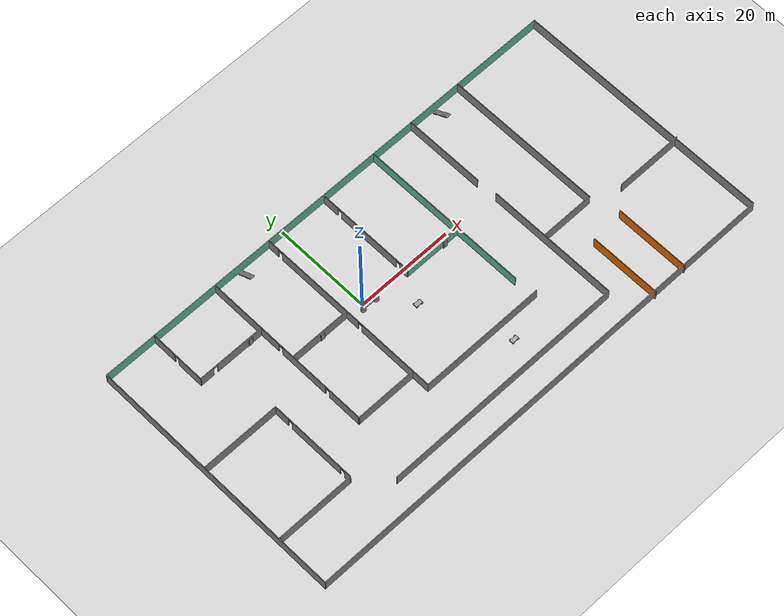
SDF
<sdf version="1.6">
 <world name="default">
  <light name="sun" type="directional">
   <pose>0 0 10 0 -0 0</pose>
   <diffuse>0.8 0.8 0.8 1</diffuse>
   <specular>0.2 0.2 0.2 1</specular>
   <attenuation>
    <range>1000</range>
    <constant>0.9</constant>
    <linear>0.01</linear>
    <quadratic>0.001</quadratic>
   </attenuation>
   <direction>-0.5 0.1 -0.9</direction>
  </light>
  <model name="ground_plane">
   <static>1</static>
   <link name="link">
    <collision name="collision">
     <geometry><plane><normal>0 0 1</normal><size>100 100</size></plane></geometry>
     <surface>
      <contact><collide_bitmask>65535</collide_bitmask></contact>
      <friction><ode><mu>100</mu><mu2>50</mu2></ode></friction>
     </surface>
    </collision>
    <visual name="visual">
     <cast_shadows>0</cast_shadows>
     <geometry><plane><normal>0 0 1</normal><size>100 100</size></plane></geometry>
     <material>
      <script><uri>file://media/materials/scripts/gazebo.material</uri><name>Gazebo/Grey</name></script>
     </material>
    </visual>
   </link>
  </model>
  <gravity>0 0 -9.8</gravity>
  <magnetic_field>6e-06 2.3e-05 -4.2e-05</magnetic_field>
  <atmosphere type="adiabatic"/>
  <physics name="default_physics" default="0" type="ode">
   <max_step_size>0.001</max_step_size>
   <real_time_factor>1</real_time_factor>
   <real_time_update_rate>1000</real_time_update_rate>
  </physics>
  <scene><ambient>0.4 0.4 0.4 1</ambient><background>0.7 0.7 0.7 1</background><shadows>1</shadows></scene>
  <spherical_coordinates>
   <surface_model>EARTH_WGS84</surface_model>
   <latitude_deg>0</latitude_deg>
   <longitude_deg>0</longitude_deg>
   <elevation>0</elevation>
   <heading_deg>0</heading_deg>
  </spherical_coordinates>
  <model name="model1">
   <link name="link_0">
    <pose>-0 0 0.4 0 -0 0</pose>
    <inertial>
     <mass>1</mass>
     <inertia>
      <ixx>0.166667</ixx>
      <ixy>0</ixy>
      <ixz>0</ixz>
      <iyy>0.166667</iyy>
      <iyz>0</iyz>
      <izz>0.166667</izz>
     </inertia>
    </inertial>
    <visual name="visual">
     <geometry><box><size>1 2 0.5</size></box></geometry>
     <material>
      <lighting>1</lighting>
      <script><uri>file://media/materials/scripts/gazebo.material</uri><name>Gazebo/Grey</name></script>
      <shader type="pixel"><normal_map>__default__</normal_map></shader>
      <ambient>0.3 0.3 0.3 1</ambient>
      <diffuse>0.7 0.7 0.7 1</diffuse>
      <specular>0.01 0.01 0.01 1</specular>
      <emissive>0 0 0 1</emissive>
     </material>
    </visual>
    <collision name="collision">
     <geometry><box><size>1 2 0.5</size></box></geometry>
     <surface>
      <friction>
       <ode><mu>1</mu><mu2>1</mu2><fdir1>0 0 0</fdir1><slip1>0</slip1><slip2>0</slip2></ode>
       <torsional>
        <coefficient>1</coefficient>
        <patch_radius>0</patch_radius>
        <surface_radius>0</surface_radius>
        <use_patch_radius>1</use_patch_radius>
        <ode><slip>0</slip></ode>
       </torsional>
      </friction>
      <bounce><restitution_coefficient>0</restitution_coefficient><threshold>1e+06</threshold></bounce>
      <contact>
       <collide_without_contact>0</collide_without_contact>
       <collide_without_contact_bitmask>1</collide_without_contact_bitmask>
       <collide_bitmask>1</collide_bitmask>
       <ode>
        <soft_cfm>0</soft_cfm>
        <soft_erp>0.2</soft_erp>
        <kp>1e+13</kp>
        <kd>1</kd>
        <max_vel>0.01</max_vel>
        <min_depth>0</min_depth>
       </ode>
       <bullet>
        <split_impulse>1</split_impulse>
        <split_impulse_penetration_threshold>-0.01</split_impulse_penetration_threshold>
        <soft_cfm>0</soft_cfm>
        <soft_erp>0.2</soft_erp>
        <kp>1e+13</kp>
        <kd>1</kd>
       </bullet>
      </contact>
     </surface>
    </collision>
   </link>
   <link name="link_3">
    <pose>-0 1.5 0.4 0 -0 0</pose>
    <inertial>
     <mass>1</mass>
     <inertia><ixx>0.1</ixx><ixy>0</ixy><ixz>0</ixz><iyy>0.1</iyy><iyz>0</iyz><izz>0.1</izz></inertia>
    </inertial>
    <visual name="visual">
     <geometry><sphere><radius>0.5</radius></sphere></geometry>
     <material>
      <lighting>1</lighting>
      <script><uri>file://media/materials/scripts/gazebo.material</uri><name>Gazebo/Grey</name></script>
      <shader type="pixel"><normal_map>__default__</normal_map></shader>
      <ambient>0.3 0.3 0.3 1</ambient>
      <diffuse>0.7 0.7 0.7 1</diffuse>
      <specular>0.01 0.01 0.01 1</specular>
      <emissive>0 0 0 1</emissive>
     </material>
    </visual>
    <collision name="collision">
     <geometry><sphere><radius>0.5</radius></sphere></geometry>
     <surface>
      <friction>
       <ode><mu>1</mu><mu2>1</mu2><fdir1>0 0 0</fdir1><slip1>0</slip1><slip2>0</slip2></ode>
       <torsional>
        <coefficient>1</coefficient>
        <patch_radius>0</patch_radius>
        <surface_radius>0</surface_radius>
        <use_patch_radius>1</use_patch_radius>
        <ode><slip>0</slip></ode>
       </torsional>
      </friction>
      <bounce><restitution_coefficient>0</restitution_coefficient><threshold>1e+06</threshold></bounce>
      <contact>
       <collide_without_contact>0</collide_without_contact>
       <collide_without_contact_bitmask>1</collide_without_contact_bitmask>
       <collide_bitmask>1</collide_bitmask>
       <ode>
        <soft_cfm>0</soft_cfm>
        <soft_erp>0.2</soft_erp>
        <kp>1e+13</kp>
        <kd>1</kd>
        <max_vel>0.01</max_vel>
        <min_depth>0</min_depth>
       </ode>
       <bullet>
        <split_impulse>1</split_impulse>
        <split_impulse_penetration_threshold>-0.01</split_impulse_penetration_threshold>
        <soft_cfm>0</soft_cfm>
        <soft_erp>0.2</soft_erp>
        <kp>1e+13</kp>
        <kd>1</kd>
       </bullet>
      </contact>
     </surface>
    </collision>
   </link>
   <link name="link_4">
    <pose>-0 1.5 -0.6 0 -0 0</pose>
    <inertial>
     <mass>1</mass>
     <inertia><ixx>0.145833</ixx><ixy>0</ixy><ixz>0</ixz><iyy>0.145833</iyy><iyz>0</iyz><izz>0.125</izz></inertia>
    </inertial>
    <visual name="visual">
     <geometry><cylinder><radius>0.5</radius><length>1</length></cylinder></geometry>
     <material>
      <lighting>1</lighting>
      <script><uri>file://media/materials/scripts/gazebo.material</uri><name>Gazebo/Grey</name></script>
      <shader type="pixel"/>
      <ambient>0.3 0.3 0.3 1</ambient>
      <diffuse>0.7 0.7 0.7 1</diffuse>
      <specular>0.01 0.01 0.01 1</specular>
      <emissive>0 0 0 1</emissive>
     </material>
    </visual>
    <collision name="collision">
     <geometry><cylinder><radius>0.5</radius><length>1</length></cylinder></geometry>
     <surface>
      <friction>
       <ode><mu>1</mu><mu2>1</mu2><fdir1>0 0 0</fdir1><slip1>0</slip1><slip2>0</slip2></ode>
       <torsional>
        <coefficient>1</coefficient>
        <patch_radius>0</patch_radius>
        <surface_radius>0</surface_radius>
        <use_patch_radius>1</use_patch_radius>
        <ode><slip>0</slip></ode>
       </torsional>
      </friction>
      <bounce><restitution_coefficient>0</restitution_coefficient><threshold>1e+06</threshold></bounce>
      <contact>
       <collide_without_contact>0</collide_without_contact>
       <collide_without_contact_bitmask>1</collide_without_contact_bitmask>
       <collide_bitmask>1</collide_bitmask>
       <ode>
        <soft_cfm>0</soft_cfm>
        <soft_erp>0.2</soft_erp>
        <kp>1e+13</kp>
        <kd>1</kd>
        <max_vel>0.01</max_vel>
        <min_depth>0</min_depth>
       </ode>
       <bullet>
        <split_impulse>1</split_impulse>
        <split_impulse_penetration_threshold>-0.01</split_impulse_penetration_threshold>
        <soft_cfm>0</soft_cfm>
        <soft_erp>0.2</soft_erp>
        <kp>1e+13</kp>
        <kd>1</kd>
       </bullet>
      </contact>
     </surface>
    </collision>
   </link>
   <link name="link_5">
    <pose>-0 -1.5 0.4 0 -0 0</pose>
    <inertial>
     <mass>1</mass>
     <inertia><ixx>0.1</ixx><ixy>0</ixy><ixz>0</ixz><iyy>0.1</iyy><iyz>0</iyz><izz>0.1</izz></inertia>
    </inertial>
    <visual name="visual">
     <geometry><sphere><radius>0.5</radius></sphere></geometry>
     <material>
      <lighting>1</lighting>
      <script><uri>file://media/materials/scripts/gazebo.material</uri><name>Gazebo/Grey</name></script>
      <shader type="pixel"><normal_map>__default__</normal_map></shader>
      <ambient>0.3 0.3 0.3 1</ambient>
      <diffuse>0.7 0.7 0.7 1</diffuse>
      <specular>0.01 0.01 0.01 1</specular>
      <emissive>0 0 0 1</emissive>
     </material>
    </visual>
    <collision name="collision">
     <geometry><sphere><radius>0.5</radius></sphere></geometry>
     <surface>
      <friction>
       <ode><mu>1</mu><mu2>1</mu2><fdir1>0 0 0</fdir1><slip1>0</slip1><slip2>0</slip2></ode>
       <torsional>
        <coefficient>1</coefficient>
        <patch_radius>0</patch_radius>
        <surface_radius>0</surface_radius>
        <use_patch_radius>1</use_patch_radius>
        <ode><slip>0</slip></ode>
       </torsional>
      </friction>
      <bounce><restitution_coefficient>0</restitution_coefficient><threshold>1e+06</threshold></bounce>
      <contact>
       <collide_without_contact>0</collide_without_contact>
       <collide_without_contact_bitmask>1</collide_without_contact_bitmask>
       <collide_bitmask>1</collide_bitmask>
       <ode>
        <soft_cfm>0</soft_cfm>
        <soft_erp>0.2</soft_erp>
        <kp>1e+13</kp>
        <kd>1</kd>
        <max_vel>0.01</max_vel>
        <min_depth>0</min_depth>
       </ode>
       <bullet>
        <split_impulse>1</split_impulse>
        <split_impulse_penetration_threshold>-0.01</split_impulse_penetration_threshold>
        <soft_cfm>0</soft_cfm>
        <soft_erp>0.2</soft_erp>
        <kp>1e+13</kp>
        <kd>1</kd>
       </bullet>
      </contact>
     </surface>
    </collision>
   </link>
   <link name="link_6">
    <pose>-0 -1.5 -0.6 0 -0 0</pose>
    <inertial>
     <mass>1</mass>
     <inertia><ixx>0.145833</ixx><ixy>0</ixy><ixz>0</ixz><iyy>0.145833</iyy><iyz>0</iyz><izz>0.125</izz></inertia>
    </inertial>
    <visual name="visual">
     <geometry><cylinder><radius>0.5</radius><length>1</length></cylinder></geometry>
     <material>
      <lighting>1</lighting>
      <script><uri>file://media/materials/scripts/gazebo.material</uri><name>Gazebo/Grey</name></script>
      <shader type="pixel"/>
      <ambient>0.3 0.3 0.3 1</ambient>
      <diffuse>0.7 0.7 0.7 1</diffuse>
      <specular>0.01 0.01 0.01 1</specular>
      <emissive>0 0 0 1</emissive>
     </material>
    </visual>
    <collision name="collision">
     <geometry><cylinder><radius>0.5</radius><length>1</length></cylinder></geometry>
     <surface>
      <friction>
       <ode><mu>1</mu><mu2>1</mu2><fdir1>0 0 0</fdir1><slip1>0</slip1><slip2>0</slip2></ode>
       <torsional>
        <coefficient>1</coefficient>
        <patch_radius>0</patch_radius>
        <surface_radius>0</surface_radius>
        <use_patch_radius>1</use_patch_radius>
        <ode><slip>0</slip></ode>
       </torsional>
      </friction>
      <bounce><restitution_coefficient>0</restitution_coefficient><threshold>1e+06</threshold></bounce>
      <contact>
       <collide_without_contact>0</collide_without_contact>
       <collide_without_contact_bitmask>1</collide_without_contact_bitmask>
       <collide_bitmask>1</collide_bitmask>
       <ode>
        <soft_cfm>0</soft_cfm>
        <soft_erp>0.2</soft_erp>
        <kp>1e+13</kp>
        <kd>1</kd>
        <max_vel>0.01</max_vel>
        <min_depth>0</min_depth>
       </ode>
       <bullet>
        <split_impulse>1</split_impulse>
        <split_impulse_penetration_threshold>-0.01</split_impulse_penetration_threshold>
        <soft_cfm>0</soft_cfm>
        <soft_erp>0.2</soft_erp>
        <kp>1e+13</kp>
        <kd>1</kd>
       </bullet>
      </contact>
     </surface>
    </collision>
   </link>
   <joint name="link_0_JOINT_0" type="revolute">
    <parent>link_0</parent>
    <child>link_3</child>
    <axis>
     <xyz>0 0 1</xyz>
     <use_parent_model_frame>0</use_parent_model_frame>
     <limit>
      <lower>-1.79769e+308</lower>
      <upper>1.79769e+308</upper>
      <effort>-1</effort>
      <velocity>-1</velocity>
     </limit>
     <dynamics>
      <spring_reference>0</spring_reference>
      <spring_stiffness>0</spring_stiffness>
      <damping>0</damping>
     </dynamics>
    </axis>
    <physics>
     <ode><limit><cfm>0</cfm><erp>0.2</erp></limit><suspension><cfm>0</cfm><erp>0.2</erp></suspension></ode>
    </physics>
   </joint>
   <joint name="link_0_JOINT_1" type="revolute">
    <parent>link_0</parent>
    <child>link_5</child>
    <axis>
     <xyz>1 0 0</xyz>
     <use_parent_model_frame>0</use_parent_model_frame>
     <limit>
      <lower>-1.79769e+308</lower>
      <upper>1.79769e+308</upper>
      <effort>-1</effort>
      <velocity>-1</velocity>
     </limit>
     <dynamics>
      <spring_reference>0</spring_reference>
      <spring_stiffness>0</spring_stiffness>
      <damping>0</damping>
     </dynamics>
    </axis>
    <physics>
     <ode><limit><cfm>0</cfm><erp>0.2</erp></limit><suspension><cfm>0</cfm><erp>0.2</erp></suspension></ode>
    </physics>
   </joint>
   <joint name="link_3_JOINT_3" type="revolute">
    <parent>link_3</parent>
    <child>link_4</child>
    <axis>
     <xyz>0 0 1</xyz>
     <use_parent_model_frame>0</use_parent_model_frame>
     <limit>
      <lower>-1.79769e+308</lower>
      <upper>1.79769e+308</upper>
      <effort>-1</effort>
      <velocity>-1</velocity>
     </limit>
     <dynamics>
      <spring_reference>0</spring_reference>
      <spring_stiffness>0</spring_stiffness>
      <damping>0</damping>
     </dynamics>
    </axis>
    <physics>
     <ode><limit><cfm>0</cfm><erp>0.2</erp></limit><suspension><cfm>0</cfm><erp>0.2</erp></suspension></ode>
    </physics>
   </joint>
   <joint name="link_5_JOINT_2" type="revolute">
    <parent>link_5</parent>
    <child>link_6</child>
    <axis>
     <xyz>0 0 1</xyz>
     <use_parent_model_frame>0</use_parent_model_frame>
     <limit>
      <lower>-1.79769e+308</lower>
      <upper>1.79769e+308</upper>
      <effort>-1</effort>
      <velocity>-1</velocity>
     </limit>
     <dynamics>
      <spring_reference>0</spring_reference>
      <spring_stiffness>0</spring_stiffness>
      <damping>0</damping>
     </dynamics>
    </axis>
    <physics>
     <ode><limit><cfm>0</cfm><erp>0.2</erp></limit><suspension><cfm>0</cfm><erp>0.2</erp></suspension></ode>
    </physics>
   </joint>
   <static>0</static>
   <pose>0.88903 -0.87063 1.10012 -7.5e-05 -0 -1.59251</pose>
  </model>
  <model name="building1">
   <pose>10.3935 -7.33421 0 0 -0 0</pose>
   <link name="Door_0">
    <collision name="Door_0_Collision">
     <geometry><box><size>0.9 0.17 2</size></box></geometry>
     <pose>0 0 1 0 -0 0</pose>
    </collision>
    <visual name="Door_0_Visual">
     <pose>0 0 1 0 -0 0</pose>
     <geometry><box><size>0.9 0.17 2</size></box></geometry>
     <material>
      <script><uri>file://media/materials/scripts/gazebo.material</uri><name>Gazebo/Grey</name></script>
     </material>
    </visual>
    <pose>7.78162 5.61116 0 0 -0 0</pose>
   </link>
   <link name="Door_4">
    <collision name="Door_4_Collision">
     <geometry><box><size>0.9 0.17 2</size></box></geometry>
     <pose>0 0 1 0 -0 0</pose>
    </collision>
    <visual name="Door_4_Visual">
     <pose>0 0 1 0 -0 0</pose>
     <geometry><box><size>0.9 0.17 2</size></box></geometry>
     <material>
      <script><uri>file://media/materials/scripts/gazebo.material</uri><name>Gazebo/Grey</name></script>
     </material>
    </visual>
    <pose>-29.1903 15.0893 0 0 -0 0</pose>
   </link>
   <link name="Door_8">
    <collision name="Door_8_Collision">
     <geometry><box><size>0.9 0.17 2</size></box></geometry>
     <pose>0 0 1 0 -0 0</pose>
    </collision>
    <visual name="Door_8_Visual">
     <pose>0 0 1 0 -0 0</pose>
     <geometry><box><size>0.9 0.17 2</size></box></geometry>
     <material>
      <script><uri>file://media/materials/scripts/gazebo.material</uri><name>Gazebo/Grey</name></script>
     </material>
    </visual>
    <pose>-19.8614 7.23332 0 0 -0 0</pose>
   </link>
   <link name="Stairs_0">
    <visual name="Stairs_0_Visual_0">
     <pose>25.8503 26.4424 0.083333 0 -0 0</pose>
     <geometry><box><size>1 0.233333 0.166667</size></box></geometry>
     <material>
      <script><uri>file://media/materials/scripts/gazebo.material</uri><name>Gazebo/Grey</name></script>
      <ambient>1 1 1 1</ambient>
     </material>
     <meta><layer>0</layer></meta>
    </visual>
    <collision name="Stairs_0_Collision_0">
     <geometry><box><size>1 0.233333 0.166667</size></box></geometry>
     <pose>25.8503 26.4424 0.083333 0 -0 0</pose>
    </collision>
    <visual name="Stairs_0_Visual_1">
     <pose>25.8503 26.2091 0.25 0 -0 0</pose>
     <geometry><box><size>1 0.233333 0.166667</size></box></geometry>
     <material>
      <script><uri>file://media/materials/scripts/gazebo.material</uri><name>Gazebo/Grey</name></script>
      <ambient>1 1 1 1</ambient>
     </material>
     <meta><layer>0</layer></meta>
    </visual>
    <collision name="Stairs_0_Collision_1">
     <geometry><box><size>1 0.233333 0.166667</size></box></geometry>
     <pose>25.8503 26.2091 0.25 0 -0 0</pose>
    </collision>
    <visual name="Stairs_0_Visual_2">
     <pose>25.8503 25.9758 0.416667 0 -0 0</pose>
     <geometry><box><size>1 0.233333 0.166667</size></box></geometry>
     <material>
      <script><uri>file://media/materials/scripts/gazebo.material</uri><name>Gazebo/Grey</name></script>
      <ambient>1 1 1 1</ambient>
     </material>
     <meta><layer>0</layer></meta>
    </visual>
    <collision name="Stairs_0_Collision_2">
     <geometry><box><size>1 0.233333 0.166667</size></box></geometry>
     <pose>25.8503 25.9758 0.416667 0 -0 0</pose>
    </collision>
    <visual name="Stairs_0_Visual_3">
     <pose>25.8503 25.7424 0.583333 0 -0 0</pose>
     <geometry><box><size>1 0.233333 0.166667</size></box></geometry>
     <material>
      <script><uri>file://media/materials/scripts/gazebo.material</uri><name>Gazebo/Grey</name></script>
      <ambient>1 1 1 1</ambient>
     </material>
     <meta><layer>0</layer></meta>
    </visual>
    <collision name="Stairs_0_Collision_3">
     <geometry><box><size>1 0.233333 0.166667</size></box></geometry>
     <pose>25.8503 25.7424 0.583333 0 -0 0</pose>
    </collision>
    <visual name="Stairs_0_Visual_4">
     <pose>25.8503 25.5091 0.75 0 -0 0</pose>
     <geometry><box><size>1 0.233333 0.166667</size></box></geometry>
     <material>
      <script><uri>file://media/materials/scripts/gazebo.material</uri><name>Gazebo/Grey</name></script>
      <ambient>1 1 1 1</ambient>
     </material>
     <meta><layer>0</layer></meta>
    </visual>
    <collision name="Stairs_0_Collision_4">
     <geometry><box><size>1 0.233333 0.166667</size></box></geometry>
     <pose>25.8503 25.5091 0.75 0 -0 0</pose>
    </collision>
    <visual name="Stairs_0_Visual_5">
     <pose>25.8503 25.2758 0.916667 0 -0 0</pose>
     <geometry><box><size>1 0.233333 0.166667</size></box></geometry>
     <material>
      <script><uri>file://media/materials/scripts/gazebo.material</uri><name>Gazebo/Grey</name></script>
      <ambient>1 1 1 1</ambient>
     </material>
     <meta><layer>0</layer></meta>
    </visual>
    <collision name="Stairs_0_Collision_5">
     <geometry><box><size>1 0.233333 0.166667</size></box></geometry>
     <pose>25.8503 25.2758 0.916667 0 -0 0</pose>
    </collision>
    <visual name="Stairs_0_Visual_6">
     <pose>25.8503 25.0424 1.08333 0 -0 0</pose>
     <geometry><box><size>1 0.233333 0.166667</size></box></geometry>
     <material>
      <script><uri>file://media/materials/scripts/gazebo.material</uri><name>Gazebo/Grey</name></script>
      <ambient>1 1 1 1</ambient>
     </material>
     <meta><layer>0</layer></meta>
    </visual>
    <collision name="Stairs_0_Collision_6">
     <geometry><box><size>1 0.233333 0.166667</size></box></geometry>
     <pose>25.8503 25.0424 1.08333 0 -0 0</pose>
    </collision>
    <visual name="Stairs_0_Visual_7">
     <pose>25.8503 24.8091 1.25 0 -0 0</pose>
     <geometry><box><size>1 0.233333 0.166667</size></box></geometry>
     <material>
      <script><uri>file://media/materials/scripts/gazebo.material</uri><name>Gazebo/Grey</name></script>
      <ambient>1 1 1 1</ambient>
     </material>
     <meta><layer>0</layer></meta>
    </visual>
    <collision name="Stairs_0_Collision_7">
     <geometry><box><size>1 0.233333 0.166667</size></box></geometry>
     <pose>25.8503 24.8091 1.25 0 -0 0</pose>
    </collision>
    <visual name="Stairs_0_Visual_8">
     <pose>25.8503 24.5758 1.41667 0 -0 0</pose>
     <geometry><box><size>1 0.233333 0.166667</size></box></geometry>
     <material>
      <script><uri>file://media/materials/scripts/gazebo.material</uri><name>Gazebo/Grey</name></script>
      <ambient>1 1 1 1</ambient>
     </material>
     <meta><layer>0</layer></meta>
    </visual>
    <collision name="Stairs_0_Collision_8">
     <geometry><box><size>1 0.233333 0.166667</size></box></geometry>
     <pose>25.8503 24.5758 1.41667 0 -0 0</pose>
    </collision>
    <visual name="Stairs_0_Visual_9">
     <pose>25.8503 24.3424 1.58333 0 -0 0</pose>
     <geometry><box><size>1 0.233333 0.166667</size></box></geometry>
     <material>
      <script><uri>file://media/materials/scripts/gazebo.material</uri><name>Gazebo/Grey</name></script>
      <ambient>1 1 1 1</ambient>
     </material>
     <meta><layer>0</layer></meta>
    </visual>
    <collision name="Stairs_0_Collision_9">
     <geometry><box><size>1 0.233333 0.166667</size></box></geometry>
     <pose>25.8503 24.3424 1.58333 0 -0 0</pose>
    </collision>
    <visual name="Stairs_0_Visual_10">
     <pose>25.8503 24.1091 1.75 0 -0 0</pose>
     <geometry><box><size>1 0.233333 0.166667</size></box></geometry>
     <material>
      <script><uri>file://media/materials/scripts/gazebo.material</uri><name>Gazebo/Grey</name></script>
      <ambient>1 1 1 1</ambient>
     </material>
     <meta><layer>0</layer></meta>
    </visual>
    <collision name="Stairs_0_Collision_10">
     <geometry><box><size>1 0.233333 0.166667</size></box></geometry>
     <pose>25.8503 24.1091 1.75 0 -0 0</pose>
    </collision>
    <visual name="Stairs_0_Visual_11">
     <pose>25.8503 23.8758 1.91667 0 -0 0</pose>
     <geometry><box><size>1 0.233333 0.166667</size></box></geometry>
     <material>
      <script><uri>file://media/materials/scripts/gazebo.material</uri><name>Gazebo/Grey</name></script>
      <ambient>1 1 1 1</ambient>
     </material>
     <meta><layer>0</layer></meta>
    </visual>
    <collision name="Stairs_0_Collision_11">
     <geometry><box><size>1 0.233333 0.166667</size></box></geometry>
     <pose>25.8503 23.8758 1.91667 0 -0 0</pose>
    </collision>
    <visual name="Stairs_0_Visual_12">
     <pose>25.8503 23.6424 2.08333 0 -0 0</pose>
     <geometry><box><size>1 0.233333 0.166667</size></box></geometry>
     <material>
      <script><uri>file://media/materials/scripts/gazebo.material</uri><name>Gazebo/Grey</name></script>
      <ambient>1 1 1 1</ambient>
     </material>
     <meta><layer>0</layer></meta>
    </visual>
    <collision name="Stairs_0_Collision_12">
     <geometry><box><size>1 0.233333 0.166667</size></box></geometry>
     <pose>25.8503 23.6424 2.08333 0 -0 0</pose>
    </collision>
    <visual name="Stairs_0_Visual_13">
     <pose>25.8503 23.4091 2.25 0 -0 0</pose>
     <geometry><box><size>1 0.233333 0.166667</size></box></geometry>
     <material>
      <script><uri>file://media/materials/scripts/gazebo.material</uri><name>Gazebo/Grey</name></script>
      <ambient>1 1 1 1</ambient>
     </material>
     <meta><layer>0</layer></meta>
    </visual>
    <collision name="Stairs_0_Collision_13">
     <geometry><box><size>1 0.233333 0.166667</size></box></geometry>
     <pose>25.8503 23.4091 2.25 0 -0 0</pose>
    </collision>
    <visual name="Stairs_0_Visual_14">
     <pose>25.8503 23.1758 2.41667 0 -0 0</pose>
     <geometry><box><size>1 0.233333 0.166667</size></box></geometry>
     <material>
      <script><uri>file://media/materials/scripts/gazebo.material</uri><name>Gazebo/Grey</name></script>
      <ambient>1 1 1 1</ambient>
     </material>
     <meta><layer>0</layer></meta>
    </visual>
    <collision name="Stairs_0_Collision_14">
     <geometry><box><size>1 0.233333 0.166667</size></box></geometry>
     <pose>25.8503 23.1758 2.41667 0 -0 0</pose>
    </collision>
   </link>
   <link name="Stairs_1">
    <visual name="Stairs_1_Visual_0">
     <pose>-21.0203 26.752 0.083333 0 -0 0</pose>
     <geometry><box><size>1 0.233333 0.166667</size></box></geometry>
     <material>
      <script><uri>file://media/materials/scripts/gazebo.material</uri><name>Gazebo/Grey</name></script>
      <ambient>1 1 1 1</ambient>
     </material>
     <meta><layer>0</layer></meta>
    </visual>
    <collision name="Stairs_1_Collision_0">
     <geometry><box><size>1 0.233333 0.166667</size></box></geometry>
     <pose>-21.0203 26.752 0.083333 0 -0 0</pose>
    </collision>
    <visual name="Stairs_1_Visual_1">
     <pose>-21.0203 26.5186 0.25 0 -0 0</pose>
     <geometry><box><size>1 0.233333 0.166667</size></box></geometry>
     <material>
      <script><uri>file://media/materials/scripts/gazebo.material</uri><name>Gazebo/Grey</name></script>
      <ambient>1 1 1 1</ambient>
     </material>
     <meta><layer>0</layer></meta>
    </visual>
    <collision name="Stairs_1_Collision_1">
     <geometry><box><size>1 0.233333 0.166667</size></box></geometry>
     <pose>-21.0203 26.5186 0.25 0 -0 0</pose>
    </collision>
    <visual name="Stairs_1_Visual_2">
     <pose>-21.0203 26.2853 0.416667 0 -0 0</pose>
     <geometry><box><size>1 0.233333 0.166667</size></box></geometry>
     <material>
      <script><uri>file://media/materials/scripts/gazebo.material</uri><name>Gazebo/Grey</name></script>
      <ambient>1 1 1 1</ambient>
     </material>
     <meta><layer>0</layer></meta>
    </visual>
    <collision name="Stairs_1_Collision_2">
     <geometry><box><size>1 0.233333 0.166667</size></box></geometry>
     <pose>-21.0203 26.2853 0.416667 0 -0 0</pose>
    </collision>
    <visual name="Stairs_1_Visual_3">
     <pose>-21.0203 26.052 0.583333 0 -0 0</pose>
     <geometry><box><size>1 0.233333 0.166667</size></box></geometry>
     <material>
      <script><uri>file://media/materials/scripts/gazebo.material</uri><name>Gazebo/Grey</name></script>
      <ambient>1 1 1 1</ambient>
     </material>
     <meta><layer>0</layer></meta>
    </visual>
    <collision name="Stairs_1_Collision_3">
     <geometry><box><size>1 0.233333 0.166667</size></box></geometry>
     <pose>-21.0203 26.052 0.583333 0 -0 0</pose>
    </collision>
    <visual name="Stairs_1_Visual_4">
     <pose>-21.0203 25.8186 0.75 0 -0 0</pose>
     <geometry><box><size>1 0.233333 0.166667</size></box></geometry>
     <material>
      <script><uri>file://media/materials/scripts/gazebo.material</uri><name>Gazebo/Grey</name></script>
      <ambient>1 1 1 1</ambient>
     </material>
     <meta><layer>0</layer></meta>
    </visual>
    <collision name="Stairs_1_Collision_4">
     <geometry><box><size>1 0.233333 0.166667</size></box></geometry>
     <pose>-21.0203 25.8186 0.75 0 -0 0</pose>
    </collision>
    <visual name="Stairs_1_Visual_5">
     <pose>-21.0203 25.5853 0.916667 0 -0 0</pose>
     <geometry><box><size>1 0.233333 0.166667</size></box></geometry>
     <material>
      <script><uri>file://media/materials/scripts/gazebo.material</uri><name>Gazebo/Grey</name></script>
      <ambient>1 1 1 1</ambient>
     </material>
     <meta><layer>0</layer></meta>
    </visual>
    <collision name="Stairs_1_Collision_5">
     <geometry><box><size>1 0.233333 0.166667</size></box></geometry>
     <pose>-21.0203 25.5853 0.916667 0 -0 0</pose>
    </collision>
    <visual name="Stairs_1_Visual_6">
     <pose>-21.0203 25.352 1.08333 0 -0 0</pose>
     <geometry><box><size>1 0.233333 0.166667</size></box></geometry>
     <material>
      <script><uri>file://media/materials/scripts/gazebo.material</uri><name>Gazebo/Grey</name></script>
      <ambient>1 1 1 1</ambient>
     </material>
     <meta><layer>0</layer></meta>
    </visual>
    <collision name="Stairs_1_Collision_6">
     <geometry><box><size>1 0.233333 0.166667</size></box></geometry>
     <pose>-21.0203 25.352 1.08333 0 -0 0</pose>
    </collision>
    <visual name="Stairs_1_Visual_7">
     <pose>-21.0203 25.1186 1.25 0 -0 0</pose>
     <geometry><box><size>1 0.233333 0.166667</size></box></geometry>
     <material>
      <script><uri>file://media/materials/scripts/gazebo.material</uri><name>Gazebo/Grey</name></script>
      <ambient>1 1 1 1</ambient>
     </material>
     <meta><layer>0</layer></meta>
    </visual>
    <collision name="Stairs_1_Collision_7">
     <geometry><box><size>1 0.233333 0.166667</size></box></geometry>
     <pose>-21.0203 25.1186 1.25 0 -0 0</pose>
    </collision>
    <visual name="Stairs_1_Visual_8">
     <pose>-21.0203 24.8853 1.41667 0 -0 0</pose>
     <geometry><box><size>1 0.233333 0.166667</size></box></geometry>
     <material>
      <script><uri>file://media/materials/scripts/gazebo.material</uri><name>Gazebo/Grey</name></script>
      <ambient>1 1 1 1</ambient>
     </material>
     <meta><layer>0</layer></meta>
    </visual>
    <collision name="Stairs_1_Collision_8">
     <geometry><box><size>1 0.233333 0.166667</size></box></geometry>
     <pose>-21.0203 24.8853 1.41667 0 -0 0</pose>
    </collision>
    <visual name="Stairs_1_Visual_9">
     <pose>-21.0203 24.652 1.58333 0 -0 0</pose>
     <geometry><box><size>1 0.233333 0.166667</size></box></geometry>
     <material>
      <script><uri>file://media/materials/scripts/gazebo.material</uri><name>Gazebo/Grey</name></script>
      <ambient>1 1 1 1</ambient>
     </material>
     <meta><layer>0</layer></meta>
    </visual>
    <collision name="Stairs_1_Collision_9">
     <geometry><box><size>1 0.233333 0.166667</size></box></geometry>
     <pose>-21.0203 24.652 1.58333 0 -0 0</pose>
    </collision>
    <visual name="Stairs_1_Visual_10">
     <pose>-21.0203 24.4186 1.75 0 -0 0</pose>
     <geometry><box><size>1 0.233333 0.166667</size></box></geometry>
     <material>
      <script><uri>file://media/materials/scripts/gazebo.material</uri><name>Gazebo/Grey</name></script>
      <ambient>1 1 1 1</ambient>
     </material>
     <meta><layer>0</layer></meta>
    </visual>
    <collision name="Stairs_1_Collision_10">
     <geometry><box><size>1 0.233333 0.166667</size></box></geometry>
     <pose>-21.0203 24.4186 1.75 0 -0 0</pose>
    </collision>
    <visual name="Stairs_1_Visual_11">
     <pose>-21.0203 24.1853 1.91667 0 -0 0</pose>
     <geometry><box><size>1 0.233333 0.166667</size></box></geometry>
     <material>
      <script><uri>file://media/materials/scripts/gazebo.material</uri><name>Gazebo/Grey</name></script>
      <ambient>1 1 1 1</ambient>
     </material>
     <meta><layer>0</layer></meta>
    </visual>
    <collision name="Stairs_1_Collision_11">
     <geometry><box><size>1 0.233333 0.166667</size></box></geometry>
     <pose>-21.0203 24.1853 1.91667 0 -0 0</pose>
    </collision>
    <visual name="Stairs_1_Visual_12">
     <pose>-21.0203 23.952 2.08333 0 -0 0</pose>
     <geometry><box><size>1 0.233333 0.166667</size></box></geometry>
     <material>
      <script><uri>file://media/materials/scripts/gazebo.material</uri><name>Gazebo/Grey</name></script>
      <ambient>1 1 1 1</ambient>
     </material>
     <meta><layer>0</layer></meta>
    </visual>
    <collision name="Stairs_1_Collision_12">
     <geometry><box><size>1 0.233333 0.166667</size></box></geometry>
     <pose>-21.0203 23.952 2.08333 0 -0 0</pose>
    </collision>
    <visual name="Stairs_1_Visual_13">
     <pose>-21.0203 23.7186 2.25 0 -0 0</pose>
     <geometry><box><size>1 0.233333 0.166667</size></box></geometry>
     <material>
      <script><uri>file://media/materials/scripts/gazebo.material</uri><name>Gazebo/Grey</name></script>
      <ambient>1 1 1 1</ambient>
     </material>
     <meta><layer>0</layer></meta>
    </visual>
    <collision name="Stairs_1_Collision_13">
     <geometry><box><size>1 0.233333 0.166667</size></box></geometry>
     <pose>-21.0203 23.7186 2.25 0 -0 0</pose>
    </collision>
    <visual name="Stairs_1_Visual_14">
     <pose>-21.0203 23.4853 2.41667 0 -0 0</pose>
     <geometry><box><size>1 0.233333 0.166667</size></box></geometry>
     <material>
      <script><uri>file://media/materials/scripts/gazebo.material</uri><name>Gazebo/Grey</name></script>
      <ambient>1 1 1 1</ambient>
     </material>
     <meta><layer>0</layer></meta>
    </visual>
    <collision name="Stairs_1_Collision_14">
     <geometry><box><size>1 0.233333 0.166667</size></box></geometry>
     <pose>-21.0203 23.4853 2.41667 0 -0 0</pose>
    </collision>
   </link>
   <link name="Wall_0">
    <collision name="Wall_0_Collision">
     <geometry><box><size>53.5 0.15 2.5</size></box></geometry>
     <pose>0 0 1.25 0 -0 0</pose>
    </collision>
    <visual name="Wall_0_Visual">
     <pose>0 0 1.25 0 -0 0</pose>
     <geometry><box><size>53.5 0.15 2.5</size></box></geometry>
     <material>
      <script><uri>file://media/materials/scripts/gazebo.material</uri><name>Gazebo/Grey</name></script>
      <ambient>1 1 1 1</ambient>
     </material>
     <meta><layer>0</layer></meta>
    </visual>
    <pose>-51.3545 0.110213 0 0 0 -1.5708</pose>
   </link>
   <link name="Wall_1">
    <collision name="Wall_1_Collision">
     <geometry><box><size>102.5 0.15 2.5</size></box></geometry>
     <pose>0 0 1.25 0 -0 0</pose>
    </collision>
    <visual name="Wall_1_Visual">
     <pose>0 0 1.25 0 -0 0</pose>
     <geometry><box><size>102.5 0.15 2.5</size></box></geometry>
     <material>
      <script><uri>file://media/materials/scripts/gazebo.material</uri><name>Gazebo/Grey</name></script>
      <ambient>1 1 1 1</ambient>
     </material>
     <meta><layer>0</layer></meta>
    </visual>
    <pose>-0.179399 -26.5648 0 0 0 -1e-06</pose>
   </link>
   <link name="Wall_10">
    <collision name="Wall_10_Collision">
     <geometry><box><size>35 0.15 2.5</size></box></geometry>
     <pose>0 0 1.25 0 -0 0</pose>
    </collision>
    <visual name="Wall_10_Visual">
     <pose>0 0 1.25 0 -0 0</pose>
     <geometry><box><size>35 0.15 2.5</size></box></geometry>
     <material>
      <script><uri>file://media/materials/scripts/gazebo.material</uri><name>Gazebo/Grey</name></script>
      <ambient>0.435294 0.796078 0.67451 1</ambient>
     </material>
     <meta><layer>0</layer></meta>
    </visual>
    <pose>10.9813 9.26626 0 0 0 -1.5708</pose>
   </link>
   <link name="Wall_12">
    <pose>-1.06449 16.203 0 0 0 -1.5708</pose>
    <visual name="Wall_12_Visual_0">
     <pose>-8.66059 0 1.25 0 -0 0</pose>
     <geometry><box><size>3.42882 0.15 2.5</size></box></geometry>
     <material>
      <script><uri>file://media/materials/scripts/gazebo.material</uri><name>Gazebo/Grey</name></script>
      <ambient>1 1 1 1</ambient>
     </material>
     <meta><layer>0</layer></meta>
    </visual>
    <collision name="Wall_12_Collision_0">
     <geometry><box><size>3.42882 0.15 2.5</size></box></geometry>
     <pose>-8.66059 0 1.25 0 -0 0</pose>
    </collision>
    <visual name="Wall_12_Visual_1">
     <pose>0.762023 0 1.25 0 -0 0</pose>
     <geometry><box><size>13.6164 0.15 2.5</size></box></geometry>
     <material>
      <script><uri>file://media/materials/scripts/gazebo.material</uri><name>Gazebo/Grey</name></script>
      <ambient>1 1 1 1</ambient>
     </material>
     <meta><layer>0</layer></meta>
    </visual>
    <collision name="Wall_12_Collision_1">
     <geometry><box><size>13.6164 0.15 2.5</size></box></geometry>
     <pose>0.762023 0 1.25 0 -0 0</pose>
    </collision>
    <visual name="Wall_12_Visual_2">
     <pose>9.42261 0 1.25 0 -0 0</pose>
     <geometry><box><size>1.90477 0.15 2.5</size></box></geometry>
     <material>
      <script><uri>file://media/materials/scripts/gazebo.material</uri><name>Gazebo/Grey</name></script>
      <ambient>1 1 1 1</ambient>
     </material>
     <meta><layer>0</layer></meta>
    </visual>
    <collision name="Wall_12_Collision_2">
     <geometry><box><size>1.90477 0.15 2.5</size></box></geometry>
     <pose>9.42261 0 1.25 0 -0 0</pose>
    </collision>
    <visual name="Wall_12_Visual_3">
     <pose>-6.49618 0 2.25 0 -0 0</pose>
     <geometry><box><size>0.9 0.15 0.5</size></box></geometry>
     <material>
      <script><uri>file://media/materials/scripts/gazebo.material</uri><name>Gazebo/Grey</name></script>
      <ambient>1 1 1 1</ambient>
     </material>
     <meta><layer>0</layer></meta>
    </visual>
    <collision name="Wall_12_Collision_3">
     <geometry><box><size>0.9 0.15 0.5</size></box></geometry>
     <pose>-6.49618 0 2.25 0 -0 0</pose>
    </collision>
    <visual name="Wall_12_Visual_4">
     <pose>8.02023 0 2.25 0 -0 0</pose>
     <geometry><box><size>0.9 0.15 0.5</size></box></geometry>
     <material>
      <script><uri>file://media/materials/scripts/gazebo.material</uri><name>Gazebo/Grey</name></script>
      <ambient>1 1 1 1</ambient>
     </material>
     <meta><layer>0</layer></meta>
    </visual>
    <collision name="Wall_12_Collision_4">
     <geometry><box><size>0.9 0.15 0.5</size></box></geometry>
     <pose>8.02023 0 2.25 0 -0 0</pose>
    </collision>
   </link>
   <link name="Wall_13">
    <collision name="Wall_13_Collision">
     <geometry><box><size>12.5 0.15 2.5</size></box></geometry>
     <pose>0 0 1.25 0 -0 0</pose>
    </collision>
    <visual name="Wall_13_Visual">
     <pose>0 0 1.25 0 -0 0</pose>
     <geometry><box><size>12.5 0.15 2.5</size></box></geometry>
     <material>
      <script><uri>file://media/materials/scripts/gazebo.material</uri><name>Gazebo/Grey</name></script>
      <ambient>0.435294 0.796078 0.67451 1</ambient>
     </material>
     <meta><layer>0</layer></meta>
    </visual>
    <pose>5.11051 5.90304 0 0 -0 0</pose>
   </link>
   <link name="Wall_15">
    <collision name="Wall_15_Collision">
     <geometry><box><size>16.75 0.15 2.5</size></box></geometry>
     <pose>0 0 1.25 0 -0 0</pose>
    </collision>
    <visual name="Wall_15_Visual">
     <pose>0 0 1.25 0 -0 0</pose>
     <geometry><box><size>16.75 0.15 2.5</size></box></geometry>
     <material>
      <script><uri>file://media/materials/scripts/gazebo.material</uri><name>Gazebo/Grey</name></script>
      <ambient>1 1 1 1</ambient>
     </material>
     <meta><layer>0</layer></meta>
    </visual>
    <pose>20.2038 18.5795 0 0 0 -1.5708</pose>
   </link>
   <link name="Wall_18">
    <collision name="Wall_18_Collision">
     <geometry><box><size>27.25 0.15 2.5</size></box></geometry>
     <pose>0 0 1.25 0 -0 0</pose>
    </collision>
    <visual name="Wall_18_Visual">
     <pose>0 0 1.25 0 -0 0</pose>
     <geometry><box><size>27.25 0.15 2.5</size></box></geometry>
     <material>
      <script><uri>file://media/materials/scripts/gazebo.material</uri><name>Gazebo/Grey</name></script>
      <ambient>1 1 1 1</ambient>
     </material>
     <meta><layer>0</layer></meta>
    </visual>
    <pose>20.5803 -7.56241 0 0 0 -1.5708</pose>
   </link>
   <link name="Wall_19">
    <collision name="Wall_19_Collision">
     <geometry><box><size>50.5 0.15 2.5</size></box></geometry>
     <pose>0 0 1.25 0 -0 0</pose>
    </collision>
    <visual name="Wall_19_Visual">
     <pose>0 0 1.25 0 -0 0</pose>
     <geometry><box><size>50.5 0.15 2.5</size></box></geometry>
     <material>
      <script><uri>file://media/materials/scripts/gazebo.material</uri><name>Gazebo/Grey</name></script>
      <ambient>1 1 1 1</ambient>
     </material>
     <meta><layer>0</layer></meta>
    </visual>
    <pose>-4.59474 -21.1124 0 0 -0 3.14159</pose>
   </link>
   <link name="Wall_2">
    <collision name="Wall_2_Collision">
     <geometry><box><size>53.5 0.15 2.5</size></box></geometry>
     <pose>0 0 1.25 0 -0 0</pose>
    </collision>
    <visual name="Wall_2_Visual">
     <pose>0 0 1.25 0 -0 0</pose>
     <geometry><box><size>53.5 0.15 2.5</size></box></geometry>
     <material>
      <script><uri>file://media/materials/scripts/gazebo.material</uri><name>Gazebo/Grey</name></script>
      <ambient>1 1 1 1</ambient>
     </material>
     <meta><layer>0</layer></meta>
    </visual>
    <pose>50.9956 0.110178 0 0 -0 1.5708</pose>
   </link>
   <link name="Wall_21">
    <pose>-26.6289 8.91872 0 0 0 -1.5708</pose>
    <visual name="Wall_21_Visual_0">
     <pose>-9.81212 0 1.25 0 -0 0</pose>
     <geometry><box><size>15.8758 0.15 2.5</size></box></geometry>
     <material>
      <script><uri>file://media/materials/scripts/gazebo.material</uri><name>Gazebo/Grey</name></script>
      <ambient>1 1 1 1</ambient>
     </material>
     <meta><layer>0</layer></meta>
    </visual>
    <collision name="Wall_21_Collision_0">
     <geometry><box><size>15.8758 0.15 2.5</size></box></geometry>
     <pose>-9.81212 0 1.25 0 -0 0</pose>
    </collision>
    <visual name="Wall_21_Visual_1">
     <pose>4.30404 0 1.25 0 -0 0</pose>
     <geometry><box><size>10.5566 0.15 2.5</size></box></geometry>
     <material>
      <script><uri>file://media/materials/scripts/gazebo.material</uri><name>Gazebo/Grey</name></script>
      <ambient>1 1 1 1</ambient>
     </material>
     <meta><layer>0</layer></meta>
    </visual>
    <collision name="Wall_21_Collision_1">
     <geometry><box><size>10.5566 0.15 2.5</size></box></geometry>
     <pose>4.30404 0 1.25 0 -0 0</pose>
    </collision>
    <visual name="Wall_21_Visual_2">
     <pose>14.1162 0 1.25 0 -0 0</pose>
     <geometry><box><size>7.26767 0.15 2.5</size></box></geometry>
     <material>
      <script><uri>file://media/materials/scripts/gazebo.material</uri><name>Gazebo/Grey</name></script>
      <ambient>1 1 1 1</ambient>
     </material>
     <meta><layer>0</layer></meta>
    </visual>
    <collision name="Wall_21_Collision_2">
     <geometry><box><size>7.26767 0.15 2.5</size></box></geometry>
     <pose>14.1162 0 1.25 0 -0 0</pose>
    </collision>
    <visual name="Wall_21_Visual_3">
     <pose>-1.42425 0 2.25 0 -0 0</pose>
     <geometry><box><size>0.9 0.15 0.5</size></box></geometry>
     <material>
      <script><uri>file://media/materials/scripts/gazebo.material</uri><name>Gazebo/Grey</name></script>
      <ambient>1 1 1 1</ambient>
     </material>
     <meta><layer>0</layer></meta>
    </visual>
    <collision name="Wall_21_Collision_3">
     <geometry><box><size>0.9 0.15 0.5</size></box></geometry>
     <pose>-1.42425 0 2.25 0 -0 0</pose>
    </collision>
    <visual name="Wall_21_Visual_4">
     <pose>10.0323 0 2.25 0 -0 0</pose>
     <geometry><box><size>0.9 0.15 0.5</size></box></geometry>
     <material>
      <script><uri>file://media/materials/scripts/gazebo.material</uri><name>Gazebo/Grey</name></script>
      <ambient>1 1 1 1</ambient>
     </material>
     <meta><layer>0</layer></meta>
    </visual>
    <collision name="Wall_21_Collision_4">
     <geometry><box><size>0.9 0.15 0.5</size></box></geometry>
     <pose>10.0323 0 2.25 0 -0 0</pose>
    </collision>
   </link>
   <link name="Wall_22">
    <collision name="Wall_22_Collision">
     <geometry><box><size>12.75 0.15 2.5</size></box></geometry>
     <pose>0 0 1.25 0 -0 0</pose>
    </collision>
    <visual name="Wall_22_Visual">
     <pose>0 0 1.25 0 -0 0</pose>
     <geometry><box><size>12.75 0.15 2.5</size></box></geometry>
     <material>
      <script><uri>file://media/materials/scripts/gazebo.material</uri><name>Gazebo/Grey</name></script>
      <ambient>1 1 1 1</ambient>
     </material>
     <meta><layer>0</layer></meta>
    </visual>
    <pose>-20.329 -8.75628 0 0 -0 0</pose>
   </link>
   <link name="Wall_24">
    <collision name="Wall_24_Collision">
     <geometry><box><size>12.5 0.15 2.5</size></box></geometry>
     <pose>0 0 1.25 0 -0 0</pose>
    </collision>
    <visual name="Wall_24_Visual">
     <pose>0 0 1.25 0 -0 0</pose>
     <geometry><box><size>12.5 0.15 2.5</size></box></geometry>
     <material>
      <script><uri>file://media/materials/scripts/gazebo.material</uri><name>Gazebo/Grey</name></script>
      <ambient>1 1 1 1</ambient>
     </material>
     <meta><layer>0</layer></meta>
    </visual>
    <pose>-20.2657 7.39577 0 0 -0 0</pose>
   </link>
   <link name="Wall_26">
    <pose>-40.5569 20.9819 0 0 0 -1.5708</pose>
    <visual name="Wall_26_Visual_0">
     <pose>-3.24397 0 1.25 0 -0 0</pose>
     <geometry><box><size>5.26205 0.15 2.5</size></box></geometry>
     <material>
      <script><uri>file://media/materials/scripts/gazebo.material</uri><name>Gazebo/Grey</name></script>
      <ambient>1 1 1 1</ambient>
     </material>
     <meta><layer>0</layer></meta>
    </visual>
    <collision name="Wall_26_Collision_0">
     <geometry><box><size>5.26205 0.15 2.5</size></box></geometry>
     <pose>-3.24397 0 1.25 0 -0 0</pose>
    </collision>
    <visual name="Wall_26_Visual_1">
     <pose>3.08103 0 1.25 0 -0 0</pose>
     <geometry><box><size>5.58795 0.15 2.5</size></box></geometry>
     <material>
      <script><uri>file://media/materials/scripts/gazebo.material</uri><name>Gazebo/Grey</name></script>
      <ambient>1 1 1 1</ambient>
     </material>
     <meta><layer>0</layer></meta>
    </visual>
    <collision name="Wall_26_Collision_1">
     <geometry><box><size>5.58795 0.15 2.5</size></box></geometry>
     <pose>3.08103 0 1.25 0 -0 0</pose>
    </collision>
    <visual name="Wall_26_Visual_2">
     <pose>-0.162948 0 2.25 0 -0 0</pose>
     <geometry><box><size>0.9 0.15 0.5</size></box></geometry>
     <material>
      <script><uri>file://media/materials/scripts/gazebo.material</uri><name>Gazebo/Grey</name></script>
      <ambient>1 1 1 1</ambient>
     </material>
     <meta><layer>0</layer></meta>
    </visual>
    <collision name="Wall_26_Collision_2">
     <geometry><box><size>0.9 0.15 0.5</size></box></geometry>
     <pose>-0.162948 0 2.25 0 -0 0</pose>
    </collision>
   </link>
   <link name="Wall_27">
    <pose>-33.6319 15.1819 0 0 -0 0</pose>
    <visual name="Wall_27_Visual_0">
     <pose>-5.51402 0 1.25 0 -0 0</pose>
     <geometry><box><size>2.97196 0.15 2.5</size></box></geometry>
     <material>
      <script><uri>file://media/materials/scripts/gazebo.material</uri><name>Gazebo/Grey</name></script>
      <ambient>1 1 1 1</ambient>
     </material>
     <meta><layer>0</layer></meta>
    </visual>
    <collision name="Wall_27_Collision_0">
     <geometry><box><size>2.97196 0.15 2.5</size></box></geometry>
     <pose>-5.51402 0 1.25 0 -0 0</pose>
    </collision>
    <visual name="Wall_27_Visual_1">
     <pose>1.93598 0 1.25 0 -0 0</pose>
     <geometry><box><size>10.128 0.15 2.5</size></box></geometry>
     <material>
      <script><uri>file://media/materials/scripts/gazebo.material</uri><name>Gazebo/Grey</name></script>
      <ambient>1 1 1 1</ambient>
     </material>
     <meta><layer>0</layer></meta>
    </visual>
    <collision name="Wall_27_Collision_1">
     <geometry><box><size>10.128 0.15 2.5</size></box></geometry>
     <pose>1.93598 0 1.25 0 -0 0</pose>
    </collision>
    <visual name="Wall_27_Visual_2">
     <pose>-3.57803 0 2.25 0 -0 0</pose>
     <geometry><box><size>0.9 0.15 0.5</size></box></geometry>
     <material>
      <script><uri>file://media/materials/scripts/gazebo.material</uri><name>Gazebo/Grey</name></script>
      <ambient>1 1 1 1</ambient>
     </material>
     <meta><layer>0</layer></meta>
    </visual>
    <collision name="Wall_27_Collision_2">
     <geometry><box><size>0.9 0.15 0.5</size></box></geometry>
     <pose>-3.57803 0 2.25 0 -0 0</pose>
    </collision>
   </link>
   <link name="Wall_29">
    <collision name="Wall_29_Collision">
     <geometry><box><size>16.25 0.15 2.5</size></box></geometry>
     <pose>0 0 1.25 0 -0 0</pose>
    </collision>
    <visual name="Wall_29_Visual">
     <pose>0 0 1.25 0 -0 0</pose>
     <geometry><box><size>16.25 0.15 2.5</size></box></geometry>
     <material>
      <script><uri>file://media/materials/scripts/gazebo.material</uri><name>Gazebo/Grey</name></script>
      <ambient>1 1 1 1</ambient>
     </material>
     <meta><layer>0</layer></meta>
    </visual>
    <pose>-43.2351 2.50217 0 0 -0 0</pose>
   </link>
   <link name="Wall_3">
    <collision name="Wall_3_Collision">
     <geometry><box><size>102.5 0.15 2.5</size></box></geometry>
     <pose>0 0 1.25 0 -0 0</pose>
    </collision>
    <visual name="Wall_3_Visual">
     <pose>0 0 1.25 0 -0 0</pose>
     <geometry><box><size>102.5 0.15 2.5</size></box></geometry>
     <material>
      <script><uri>file://media/materials/scripts/gazebo.material</uri><name>Gazebo/Grey</name></script>
      <ambient>0.435294 0.796078 0.67451 1</ambient>
     </material>
     <meta><layer>0</layer></meta>
    </visual>
    <pose>-0.179496 26.7852 0 0 -0 3.14159</pose>
   </link>
   <link name="Wall_30">
    <pose>-35.1851 -6.54783 0 0 0 -1.5708</pose>
    <visual name="Wall_30_Visual_0">
     <pose>-7.50461 0 1.25 0 -0 0</pose>
     <geometry><box><size>3.24078 0.15 2.5</size></box></geometry>
     <material>
      <script><uri>file://media/materials/scripts/gazebo.material</uri><name>Gazebo/Grey</name></script>
      <ambient>1 1 1 1</ambient>
     </material>
     <meta><layer>0</layer></meta>
    </visual>
    <collision name="Wall_30_Collision_0">
     <geometry><box><size>3.24078 0.15 2.5</size></box></geometry>
     <pose>-7.50461 0 1.25 0 -0 0</pose>
    </collision>
    <visual name="Wall_30_Visual_1">
     <pose>0.866901 0 1.25 0 -0 0</pose>
     <geometry><box><size>11.7022 0.15 2.5</size></box></geometry>
     <material>
      <script><uri>file://media/materials/scripts/gazebo.material</uri><name>Gazebo/Grey</name></script>
      <ambient>1 1 1 1</ambient>
     </material>
     <meta><layer>0</layer></meta>
    </visual>
    <collision name="Wall_30_Collision_1">
     <geometry><box><size>11.7022 0.15 2.5</size></box></geometry>
     <pose>0.866901 0 1.25 0 -0 0</pose>
    </collision>
    <visual name="Wall_30_Visual_2">
     <pose>8.37151 0 1.25 0 -0 0</pose>
     <geometry><box><size>1.50698 0.15 2.5</size></box></geometry>
     <material>
      <script><uri>file://media/materials/scripts/gazebo.material</uri><name>Gazebo/Grey</name></script>
      <ambient>1 1 1 1</ambient>
     </material>
     <meta><layer>0</layer></meta>
    </visual>
    <collision name="Wall_30_Collision_2">
     <geometry><box><size>1.50698 0.15 2.5</size></box></geometry>
     <pose>8.37151 0 1.25 0 -0 0</pose>
    </collision>
    <visual name="Wall_30_Visual_3">
     <pose>-5.43422 0 2.25 0 -0 0</pose>
     <geometry><box><size>0.9 0.15 0.5</size></box></geometry>
     <material>
      <script><uri>file://media/materials/scripts/gazebo.material</uri><name>Gazebo/Grey</name></script>
      <ambient>1 1 1 1</ambient>
     </material>
     <meta><layer>0</layer></meta>
    </visual>
    <collision name="Wall_30_Collision_3">
     <geometry><box><size>0.9 0.15 0.5</size></box></geometry>
     <pose>-5.43422 0 2.25 0 -0 0</pose>
    </collision>
    <visual name="Wall_30_Visual_4">
     <pose>7.16802 0 2.25 0 -0 0</pose>
     <geometry><box><size>0.9 0.15 0.5</size></box></geometry>
     <material>
      <script><uri>file://media/materials/scripts/gazebo.material</uri><name>Gazebo/Grey</name></script>
      <ambient>1 1 1 1</ambient>
     </material>
     <meta><layer>0</layer></meta>
    </visual>
    <collision name="Wall_30_Collision_4">
     <geometry><box><size>0.9 0.15 0.5</size></box></geometry>
     <pose>7.16802 0 2.25 0 -0 0</pose>
    </collision>
   </link>
   <link name="Wall_31">
    <collision name="Wall_31_Collision">
     <geometry><box><size>16 0.15 2.5</size></box></geometry>
     <pose>0 0 1.25 0 -0 0</pose>
    </collision>
    <visual name="Wall_31_Visual">
     <pose>0 0 1.25 0 -0 0</pose>
     <geometry><box><size>16 0.15 2.5</size></box></geometry>
     <material>
      <script><uri>file://media/materials/scripts/gazebo.material</uri><name>Gazebo/Grey</name></script>
      <ambient>1 1 1 1</ambient>
     </material>
     <meta><layer>0</layer></meta>
    </visual>
    <pose>-43.1101 -15.5978 0 0 -0 3.14159</pose>
   </link>
   <link name="Wall_33">
    <collision name="Wall_33_Collision">
     <geometry><box><size>32.5 0.15 2.5</size></box></geometry>
     <pose>0 0 1.25 0 -0 0</pose>
    </collision>
    <visual name="Wall_33_Visual">
     <pose>0 0 1.25 0 -0 0</pose>
     <geometry><box><size>32.5 0.15 2.5</size></box></geometry>
     <material>
      <script><uri>file://media/materials/scripts/gazebo.material</uri><name>Gazebo/Grey</name></script>
      <ambient>1 1 1 1</ambient>
     </material>
     <meta><layer>0</layer></meta>
    </visual>
    <pose>31.6902 10.4622 0 0 0 -1.5708</pose>
   </link>
   <link name="Wall_34">
    <collision name="Wall_34_Collision">
     <geometry><box><size>11.25 0.15 2.5</size></box></geometry>
     <pose>0 0 1.25 0 -0 0</pose>
    </collision>
    <visual name="Wall_34_Visual">
     <pose>0 0 1.25 0 -0 0</pose>
     <geometry><box><size>11.25 0.15 2.5</size></box></geometry>
     <material>
      <script><uri>file://media/materials/scripts/gazebo.material</uri><name>Gazebo/Grey</name></script>
      <ambient>1 1 1 1</ambient>
     </material>
     <meta><layer>0</layer></meta>
    </visual>
    <pose>26.1402 -5.71284 0 0 -0 3.14159</pose>
   </link>
   <link name="Wall_36">
    <collision name="Wall_36_Collision">
     <geometry><box><size>14.75 0.15 2.5</size></box></geometry>
     <pose>0 0 1.25 0 -0 0</pose>
    </collision>
    <visual name="Wall_36_Visual">
     <pose>0 0 1.25 0 -0 0</pose>
     <geometry><box><size>14.75 0.15 2.5</size></box></geometry>
     <material>
      <script><uri>file://media/materials/scripts/gazebo.material</uri><name>Gazebo/Grey</name></script>
      <ambient>0.996078 0.47451 0.0196078 1</ambient>
     </material>
     <meta><layer>0</layer></meta>
    </visual>
    <pose>26.2141 -19.5795 0 0 -0 1.5708</pose>
   </link>
   <link name="Wall_39">
    <collision name="Wall_39_Collision">
     <geometry><box><size>15.5 0.15 2.5</size></box></geometry>
     <pose>0 0 1.25 0 -0 0</pose>
    </collision>
    <visual name="Wall_39_Visual">
     <pose>0 0 1.25 0 -0 0</pose>
     <geometry><box><size>15.5 0.15 2.5</size></box></geometry>
     <material>
      <script><uri>file://media/materials/scripts/gazebo.material</uri><name>Gazebo/Grey</name></script>
      <ambient>0.996078 0.47451 0.0196078 1</ambient>
     </material>
     <meta><layer>0</layer></meta>
    </visual>
    <pose>33.4327 -19.1218 0 0 0 -1.5708</pose>
   </link>
   <link name="Wall_42">
    <collision name="Wall_42_Collision">
     <geometry><box><size>14 0.15 2.5</size></box></geometry>
     <pose>0 0 1.25 0 -0 0</pose>
    </collision>
    <visual name="Wall_42_Visual">
     <pose>0 0 1.25 0 -0 0</pose>
     <geometry><box><size>14 0.15 2.5</size></box></geometry>
     <material>
      <script><uri>file://media/materials/scripts/gazebo.material</uri><name>Gazebo/Grey</name></script>
      <ambient>1 1 1 1</ambient>
     </material>
     <meta><layer>0</layer></meta>
    </visual>
    <pose>44.4295 -7.96197 0 0 -0 3.14159</pose>
   </link>
   <link name="Wall_6">
    <pose>-14.0513 7.14126 0 0 0 -1.5708</pose>
    <visual name="Wall_6_Visual_0">
     <pose>-18.3858 0 1.25 0 -0 0</pose>
     <geometry><box><size>2.47849 0.15 2.5</size></box></geometry>
     <material>
      <script><uri>file://media/materials/scripts/gazebo.material</uri><name>Gazebo/Grey</name></script>
      <ambient>1 1 1 1</ambient>
     </material>
     <meta><layer>0</layer></meta>
    </visual>
    <collision name="Wall_6_Collision_0">
     <geometry><box><size>2.47849 0.15 2.5</size></box></geometry>
     <pose>-18.3858 0 1.25 0 -0 0</pose>
    </collision>
    <visual name="Wall_6_Visual_1">
     <pose>-6.80543 0 1.25 0 -0 0</pose>
     <geometry><box><size>18.8822 0.15 2.5</size></box></geometry>
     <material>
      <script><uri>file://media/materials/scripts/gazebo.material</uri><name>Gazebo/Grey</name></script>
      <ambient>1 1 1 1</ambient>
     </material>
     <meta><layer>0</layer></meta>
    </visual>
    <collision name="Wall_6_Collision_1">
     <geometry><box><size>18.8822 0.15 2.5</size></box></geometry>
     <pose>-6.80543 0 1.25 0 -0 0</pose>
    </collision>
    <visual name="Wall_6_Visual_2">
     <pose>11.5803 0 1.25 0 -0 0</pose>
     <geometry><box><size>16.0893 0.15 2.5</size></box></geometry>
     <material>
      <script><uri>file://media/materials/scripts/gazebo.material</uri><name>Gazebo/Grey</name></script>
      <ambient>1 1 1 1</ambient>
     </material>
     <meta><layer>0</layer></meta>
    </visual>
    <collision name="Wall_6_Collision_2">
     <geometry><box><size>16.0893 0.15 2.5</size></box></geometry>
     <pose>11.5803 0 1.25 0 -0 0</pose>
    </collision>
    <visual name="Wall_6_Visual_3">
     <pose>-16.6965 0 2.25 0 -0 0</pose>
     <geometry><box><size>0.9 0.15 0.5</size></box></geometry>
     <material>
      <script><uri>file://media/materials/scripts/gazebo.material</uri><name>Gazebo/Grey</name></script>
      <ambient>1 1 1 1</ambient>
     </material>
     <meta><layer>0</layer></meta>
    </visual>
    <collision name="Wall_6_Collision_3">
     <geometry><box><size>0.9 0.15 0.5</size></box></geometry>
     <pose>-16.6965 0 2.25 0 -0 0</pose>
    </collision>
    <visual name="Wall_6_Visual_4">
     <pose>3.08566 0 2.25 0 -0 0</pose>
     <geometry><box><size>0.9 0.15 0.5</size></box></geometry>
     <material>
      <script><uri>file://media/materials/scripts/gazebo.material</uri><name>Gazebo/Grey</name></script>
      <ambient>1 1 1 1</ambient>
     </material>
     <meta><layer>0</layer></meta>
    </visual>
    <collision name="Wall_6_Collision_4">
     <geometry><box><size>0.9 0.15 0.5</size></box></geometry>
     <pose>3.08566 0 2.25 0 -0 0</pose>
    </collision>
   </link>
   <link name="Wall_8">
    <collision name="Wall_8_Collision">
     <geometry><box><size>26 0.15 2.5</size></box></geometry>
     <pose>0 0 1.25 0 -0 0</pose>
    </collision>
    <visual name="Wall_8_Visual">
     <pose>0 0 1.25 0 -0 0</pose>
     <geometry><box><size>26 0.15 2.5</size></box></geometry>
     <material>
      <script><uri>file://media/materials/scripts/gazebo.material</uri><name>Gazebo/Grey</name></script>
      <ambient>1 1 1 1</ambient>
     </material>
     <meta><layer>0</layer></meta>
    </visual>
    <pose>-1.12634 -12.4087 0 0 -0 0</pose>
   </link>
   <static>1</static>
  </model>
  <model name="model_wheel">
   <link name="link_0">
    <pose>-2e-06 1e-06 0 0 -0 0</pose>
    <inertial>
     <mass>1</mass>
     <inertia>
      <ixx>0.166667</ixx>
      <ixy>0</ixy>
      <ixz>0</ixz>
      <iyy>0.166667</iyy>
      <iyz>0</iyz>
      <izz>0.166667</izz>
     </inertia>
    </inertial>
    <visual name="visual">
     <geometry><box><size>1.5 0.8 0.2</size></box></geometry>
     <material>
      <lighting>1</lighting>
      <script><uri>file://media/materials/scripts/gazebo.material</uri><name>Gazebo/Grey</name></script>
      <shader type="pixel"><normal_map>__default__</normal_map></shader>
      <ambient>0.3 0.3 0.3 1</ambient>
      <diffuse>0.7 0.7 0.7 1</diffuse>
      <specular>0.01 0.01 0.01 1</specular>
      <emissive>0 0 0 1</emissive>
     </material>
    </visual>
    <collision name="collision">
     <geometry><box><size>1.5 0.8 0.2</size></box></geometry>
     <surface>
      <friction>
       <ode><mu>1</mu><mu2>1</mu2><fdir1>0 0 0</fdir1><slip1>0</slip1><slip2>0</slip2></ode>
       <torsional>
        <coefficient>1</coefficient>
        <patch_radius>0</patch_radius>
        <surface_radius>0</surface_radius>
        <use_patch_radius>1</use_patch_radius>
        <ode><slip>0</slip></ode>
       </torsional>
      </friction>
      <bounce><restitution_coefficient>0</restitution_coefficient><threshold>1e+06</threshold></bounce>
      <contact>
       <collide_without_contact>0</collide_without_contact>
       <collide_without_contact_bitmask>1</collide_without_contact_bitmask>
       <collide_bitmask>1</collide_bitmask>
       <ode>
        <soft_cfm>0</soft_cfm>
        <soft_erp>0.2</soft_erp>
        <kp>1e+13</kp>
        <kd>1</kd>
        <max_vel>0.01</max_vel>
        <min_depth>0</min_depth>
       </ode>
       <bullet>
        <split_impulse>1</split_impulse>
        <split_impulse_penetration_threshold>-0.01</split_impulse_penetration_threshold>
        <soft_cfm>0</soft_cfm>
        <soft_erp>0.2</soft_erp>
        <kp>1e+13</kp>
        <kd>1</kd>
       </bullet>
      </contact>
     </surface>
    </collision>
   </link>
   <link name="link_1">
    <pose>-0.550002 -0.450018 0 1.5707 -0 0</pose>
    <inertial>
     <mass>1</mass>
     <inertia><ixx>0.145833</ixx><ixy>0</ixy><ixz>0</ixz><iyy>0.145833</iyy><iyz>0</iyz><izz>0.125</izz></inertia>
    </inertial>
    <visual name="visual">
     <geometry><cylinder><radius>0.2</radius><length>0.1</length></cylinder></geometry>
     <material>
      <lighting>1</lighting>
      <script><uri>file://media/materials/scripts/gazebo.material</uri><name>Gazebo/Grey</name></script>
      <shader type="pixel"><normal_map>__default__</normal_map></shader>
      <ambient>0.3 0.3 0.3 1</ambient>
      <diffuse>0.7 0.7 0.7 1</diffuse>
      <specular>0.01 0.01 0.01 1</specular>
      <emissive>0 0 0 1</emissive>
     </material>
    </visual>
    <collision name="collision">
     <geometry><cylinder><radius>0.2</radius><length>0.1</length></cylinder></geometry>
     <surface>
      <friction>
       <ode><mu>1</mu><mu2>1</mu2><fdir1>0 0 0</fdir1><slip1>0</slip1><slip2>0</slip2></ode>
       <torsional>
        <coefficient>1</coefficient>
        <patch_radius>0</patch_radius>
        <surface_radius>0</surface_radius>
        <use_patch_radius>1</use_patch_radius>
        <ode><slip>0</slip></ode>
       </torsional>
      </friction>
      <bounce><restitution_coefficient>0</restitution_coefficient><threshold>1e+06</threshold></bounce>
      <contact>
       <collide_without_contact>0</collide_without_contact>
       <collide_without_contact_bitmask>1</collide_without_contact_bitmask>
       <collide_bitmask>1</collide_bitmask>
       <ode>
        <soft_cfm>0</soft_cfm>
        <soft_erp>0.2</soft_erp>
        <kp>1e+13</kp>
        <kd>1</kd>
        <max_vel>0.01</max_vel>
        <min_depth>0</min_depth>
       </ode>
       <bullet>
        <split_impulse>1</split_impulse>
        <split_impulse_penetration_threshold>-0.01</split_impulse_penetration_threshold>
        <soft_cfm>0</soft_cfm>
        <soft_erp>0.2</soft_erp>
        <kp>1e+13</kp>
        <kd>1</kd>
       </bullet>
      </contact>
     </surface>
    </collision>
   </link>
   <link name="link_1_clone">
    <pose>0.550002 -0.450021 0 1.5707 -0 0</pose>
    <inertial>
     <mass>1</mass>
     <inertia><ixx>0.145833</ixx><ixy>0</ixy><ixz>0</ixz><iyy>0.145833</iyy><iyz>0</iyz><izz>0.125</izz></inertia>
    </inertial>
    <visual name="visual">
     <geometry><cylinder><radius>0.2</radius><length>0.1</length></cylinder></geometry>
     <material>
      <lighting>1</lighting>
      <script><uri>file://media/materials/scripts/gazebo.material</uri><name>Gazebo/Grey</name></script>
      <shader type="pixel"><normal_map>__default__</normal_map></shader>
      <ambient>0.3 0.3 0.3 1</ambient>
      <diffuse>0.7 0.7 0.7 1</diffuse>
      <specular>0.01 0.01 0.01 1</specular>
      <emissive>0 0 0 1</emissive>
     </material>
    </visual>
    <collision name="collision">
     <geometry><cylinder><radius>0.2</radius><length>0.1</length></cylinder></geometry>
     <surface>
      <friction>
       <ode><mu>1</mu><mu2>1</mu2><fdir1>0 0 0</fdir1><slip1>0</slip1><slip2>0</slip2></ode>
       <torsional>
        <coefficient>1</coefficient>
        <patch_radius>0</patch_radius>
        <surface_radius>0</surface_radius>
        <use_patch_radius>1</use_patch_radius>
        <ode><slip>0</slip></ode>
       </torsional>
      </friction>
      <bounce><restitution_coefficient>0</restitution_coefficient><threshold>1e+06</threshold></bounce>
      <contact>
       <collide_without_contact>0</collide_without_contact>
       <collide_without_contact_bitmask>1</collide_without_contact_bitmask>
       <collide_bitmask>1</collide_bitmask>
       <ode>
        <soft_cfm>0</soft_cfm>
        <soft_erp>0.2</soft_erp>
        <kp>1e+13</kp>
        <kd>1</kd>
        <max_vel>0.01</max_vel>
        <min_depth>0</min_depth>
       </ode>
       <bullet>
        <split_impulse>1</split_impulse>
        <split_impulse_penetration_threshold>-0.01</split_impulse_penetration_threshold>
        <soft_cfm>0</soft_cfm>
        <soft_erp>0.2</soft_erp>
        <kp>1e+13</kp>
        <kd>1</kd>
       </bullet>
      </contact>
     </surface>
    </collision>
   </link>
   <link name="link_1_clone_0">
    <pose>-0.550002 0.45002 0 1.5707 -0 0</pose>
    <inertial>
     <mass>1</mass>
     <inertia><ixx>0.145833</ixx><ixy>0</ixy><ixz>0</ixz><iyy>0.145833</iyy><iyz>0</iyz><izz>0.125</izz></inertia>
    </inertial>
    <visual name="visual">
     <geometry><cylinder><radius>0.2</radius><length>0.1</length></cylinder></geometry>
     <material>
      <lighting>1</lighting>
      <script><uri>file://media/materials/scripts/gazebo.material</uri><name>Gazebo/Grey</name></script>
      <shader type="pixel"><normal_map>__default__</normal_map></shader>
      <ambient>0.3 0.3 0.3 1</ambient>
      <diffuse>0.7 0.7 0.7 1</diffuse>
      <specular>0.01 0.01 0.01 1</specular>
      <emissive>0 0 0 1</emissive>
     </material>
    </visual>
    <collision name="collision">
     <geometry><cylinder><radius>0.2</radius><length>0.1</length></cylinder></geometry>
     <surface>
      <friction>
       <ode><mu>1</mu><mu2>1</mu2><fdir1>0 0 0</fdir1><slip1>0</slip1><slip2>0</slip2></ode>
       <torsional>
        <coefficient>1</coefficient>
        <patch_radius>0</patch_radius>
        <surface_radius>0</surface_radius>
        <use_patch_radius>1</use_patch_radius>
        <ode><slip>0</slip></ode>
       </torsional>
      </friction>
      <bounce><restitution_coefficient>0</restitution_coefficient><threshold>1e+06</threshold></bounce>
      <contact>
       <collide_without_contact>0</collide_without_contact>
       <collide_without_contact_bitmask>1</collide_without_contact_bitmask>
       <collide_bitmask>1</collide_bitmask>
       <ode>
        <soft_cfm>0</soft_cfm>
        <soft_erp>0.2</soft_erp>
        <kp>1e+13</kp>
        <kd>1</kd>
        <max_vel>0.01</max_vel>
        <min_depth>0</min_depth>
       </ode>
       <bullet>
        <split_impulse>1</split_impulse>
        <split_impulse_penetration_threshold>-0.01</split_impulse_penetration_threshold>
        <soft_cfm>0</soft_cfm>
        <soft_erp>0.2</soft_erp>
        <kp>1e+13</kp>
        <kd>1</kd>
       </bullet>
      </contact>
     </surface>
    </collision>
   </link>
   <link name="link_1_clone_1">
    <pose>0.549998 0.45002 0 1.5707 -0 0</pose>
    <inertial>
     <mass>1</mass>
     <inertia><ixx>0.145833</ixx><ixy>0</ixy><ixz>0</ixz><iyy>0.145833</iyy><iyz>0</iyz><izz>0.125</izz></inertia>
    </inertial>
    <visual name="visual">
     <geometry><cylinder><radius>0.2</radius><length>0.1</length></cylinder></geometry>
     <material>
      <lighting>1</lighting>
      <script><uri>file://media/materials/scripts/gazebo.material</uri><name>Gazebo/Grey</name></script>
      <shader type="pixel"><normal_map>__default__</normal_map></shader>
      <ambient>0.3 0.3 0.3 1</ambient>
      <diffuse>0.7 0.7 0.7 1</diffuse>
      <specular>0.01 0.01 0.01 1</specular>
      <emissive>0 0 0 1</emissive>
     </material>
    </visual>
    <collision name="collision">
     <geometry><cylinder><radius>0.2</radius><length>0.1</length></cylinder></geometry>
     <surface>
      <friction>
       <ode><mu>1</mu><mu2>1</mu2><fdir1>0 0 0</fdir1><slip1>0</slip1><slip2>0</slip2></ode>
       <torsional>
        <coefficient>1</coefficient>
        <patch_radius>0</patch_radius>
        <surface_radius>0</surface_radius>
        <use_patch_radius>1</use_patch_radius>
        <ode><slip>0</slip></ode>
       </torsional>
      </friction>
      <bounce><restitution_coefficient>0</restitution_coefficient><threshold>1e+06</threshold></bounce>
      <contact>
       <collide_without_contact>0</collide_without_contact>
       <collide_without_contact_bitmask>1</collide_without_contact_bitmask>
       <collide_bitmask>1</collide_bitmask>
       <ode>
        <soft_cfm>0</soft_cfm>
        <soft_erp>0.2</soft_erp>
        <kp>1e+13</kp>
        <kd>1</kd>
        <max_vel>0.01</max_vel>
        <min_depth>0</min_depth>
       </ode>
       <bullet>
        <split_impulse>1</split_impulse>
        <split_impulse_penetration_threshold>-0.01</split_impulse_penetration_threshold>
        <soft_cfm>0</soft_cfm>
        <soft_erp>0.2</soft_erp>
        <kp>1e+13</kp>
        <kd>1</kd>
       </bullet>
      </contact>
     </surface>
    </collision>
   </link>
   <joint name="link_0_JOINT_0" type="revolute">
    <parent>link_0</parent>
    <child>link_1_clone_1</child>
    <axis>
     <xyz>0 1 0</xyz>
     <use_parent_model_frame>0</use_parent_model_frame>
     <limit>
      <lower>-1.79769e+308</lower>
      <upper>1.79769e+308</upper>
      <effort>-1</effort>
      <velocity>-1</velocity>
     </limit>
     <dynamics>
      <spring_reference>0</spring_reference>
      <spring_stiffness>0</spring_stiffness>
      <damping>0</damping>
      <friction>0</friction>
     </dynamics>
    </axis>
    <physics>
     <ode><limit><cfm>0</cfm><erp>0.2</erp></limit><suspension><cfm>0</cfm><erp>0.2</erp></suspension></ode>
    </physics>
   </joint>
   <joint name="link_0_JOINT_1" type="revolute">
    <parent>link_0</parent>
    <child>link_1_clone</child>
    <axis>
     <xyz>0 1 0</xyz>
     <use_parent_model_frame>0</use_parent_model_frame>
     <limit>
      <lower>-1.79769e+308</lower>
      <upper>1.79769e+308</upper>
      <effort>-1</effort>
      <velocity>-1</velocity>
     </limit>
     <dynamics>
      <spring_reference>0</spring_reference>
      <spring_stiffness>0</spring_stiffness>
      <damping>0</damping>
      <friction>0</friction>
     </dynamics>
    </axis>
    <physics>
     <ode><limit><cfm>0</cfm><erp>0.2</erp></limit><suspension><cfm>0</cfm><erp>0.2</erp></suspension></ode>
    </physics>
   </joint>
   <joint name="link_0_JOINT_2" type="revolute">
    <parent>link_0</parent>
    <child>link_1</child>
    <axis>
     <xyz>0 1 0</xyz>
     <use_parent_model_frame>0</use_parent_model_frame>
     <limit>
      <lower>-1.79769e+308</lower>
      <upper>1.79769e+308</upper>
      <effort>-1</effort>
      <velocity>-1</velocity>
     </limit>
     <dynamics>
      <spring_reference>0</spring_reference>
      <spring_stiffness>0</spring_stiffness>
      <damping>0</damping>
      <friction>0</friction>
     </dynamics>
    </axis>
    <physics>
     <ode><limit><cfm>0</cfm><erp>0.2</erp></limit><suspension><cfm>0</cfm><erp>0.2</erp></suspension></ode>
    </physics>
   </joint>
   <joint name="link_0_JOINT_3" type="revolute">
    <parent>link_0</parent>
    <child>link_1_clone_0</child>
    <axis>
     <xyz>0 1 0</xyz>
     <use_parent_model_frame>0</use_parent_model_frame>
     <limit>
      <lower>-1.79769e+308</lower>
      <upper>1.79769e+308</upper>
      <effort>-1</effort>
      <velocity>-1</velocity>
     </limit>
     <dynamics>
      <spring_reference>0</spring_reference>
      <spring_stiffness>0</spring_stiffness>
      <damping>0</damping>
      <friction>0</friction>
     </dynamics>
    </axis>
    <physics>
     <ode><limit><cfm>0</cfm><erp>0.2</erp></limit><suspension><cfm>0</cfm><erp>0.2</erp></suspension></ode>
    </physics>
   </joint>
   <static>0</static>
   <pose>6.90031 -6.52365 0.200003 -3e-06 -1e-06 -0.019175</pose>
  </model>
  <model name="model_wheel_0">
   <link name="link_0">
    <pose>-2e-06 1e-06 0 0 -0 0</pose>
    <inertial>
     <mass>1</mass>
     <inertia>
      <ixx>0.166667</ixx>
      <ixy>0</ixy>
      <ixz>0</ixz>
      <iyy>0.166667</iyy>
      <iyz>0</iyz>
      <izz>0.166667</izz>
     </inertia>
    </inertial>
    <visual name="visual">
     <geometry><box><size>1.5 0.8 0.2</size></box></geometry>
     <material>
      <lighting>1</lighting>
      <script><uri>file://media/materials/scripts/gazebo.material</uri><name>Gazebo/Grey</name></script>
      <shader type="pixel"><normal_map>__default__</normal_map></shader>
      <ambient>0.3 0.3 0.3 1</ambient>
      <diffuse>0.7 0.7 0.7 1</diffuse>
      <specular>0.01 0.01 0.01 1</specular>
      <emissive>0 0 0 1</emissive>
     </material>
    </visual>
    <collision name="collision">
     <geometry><box><size>1.5 0.8 0.2</size></box></geometry>
     <surface>
      <friction>
       <ode><mu>1</mu><mu2>1</mu2><fdir1>0 0 0</fdir1><slip1>0</slip1><slip2>0</slip2></ode>
       <torsional>
        <coefficient>1</coefficient>
        <patch_radius>0</patch_radius>
        <surface_radius>0</surface_radius>
        <use_patch_radius>1</use_patch_radius>
        <ode><slip>0</slip></ode>
       </torsional>
      </friction>
      <bounce><restitution_coefficient>0</restitution_coefficient><threshold>1e+06</threshold></bounce>
      <contact>
       <collide_without_contact>0</collide_without_contact>
       <collide_without_contact_bitmask>1</collide_without_contact_bitmask>
       <collide_bitmask>1</collide_bitmask>
       <ode>
        <soft_cfm>0</soft_cfm>
        <soft_erp>0.2</soft_erp>
        <kp>1e+13</kp>
        <kd>1</kd>
        <max_vel>0.01</max_vel>
        <min_depth>0</min_depth>
       </ode>
       <bullet>
        <split_impulse>1</split_impulse>
        <split_impulse_penetration_threshold>-0.01</split_impulse_penetration_threshold>
        <soft_cfm>0</soft_cfm>
        <soft_erp>0.2</soft_erp>
        <kp>1e+13</kp>
        <kd>1</kd>
       </bullet>
      </contact>
     </surface>
    </collision>
   </link>
   <link name="link_1">
    <pose>-0.550002 -0.450018 0 1.5707 -0 0</pose>
    <inertial>
     <mass>1</mass>
     <inertia><ixx>0.145833</ixx><ixy>0</ixy><ixz>0</ixz><iyy>0.145833</iyy><iyz>0</iyz><izz>0.125</izz></inertia>
    </inertial>
    <visual name="visual">
     <geometry><cylinder><radius>0.2</radius><length>0.1</length></cylinder></geometry>
     <material>
      <lighting>1</lighting>
      <script><uri>file://media/materials/scripts/gazebo.material</uri><name>Gazebo/Grey</name></script>
      <shader type="pixel"><normal_map>__default__</normal_map></shader>
      <ambient>0.3 0.3 0.3 1</ambient>
      <diffuse>0.7 0.7 0.7 1</diffuse>
      <specular>0.01 0.01 0.01 1</specular>
      <emissive>0 0 0 1</emissive>
     </material>
    </visual>
    <collision name="collision">
     <geometry><cylinder><radius>0.2</radius><length>0.1</length></cylinder></geometry>
     <surface>
      <friction>
       <ode><mu>1</mu><mu2>1</mu2><fdir1>0 0 0</fdir1><slip1>0</slip1><slip2>0</slip2></ode>
       <torsional>
        <coefficient>1</coefficient>
        <patch_radius>0</patch_radius>
        <surface_radius>0</surface_radius>
        <use_patch_radius>1</use_patch_radius>
        <ode><slip>0</slip></ode>
       </torsional>
      </friction>
      <bounce><restitution_coefficient>0</restitution_coefficient><threshold>1e+06</threshold></bounce>
      <contact>
       <collide_without_contact>0</collide_without_contact>
       <collide_without_contact_bitmask>1</collide_without_contact_bitmask>
       <collide_bitmask>1</collide_bitmask>
       <ode>
        <soft_cfm>0</soft_cfm>
        <soft_erp>0.2</soft_erp>
        <kp>1e+13</kp>
        <kd>1</kd>
        <max_vel>0.01</max_vel>
        <min_depth>0</min_depth>
       </ode>
       <bullet>
        <split_impulse>1</split_impulse>
        <split_impulse_penetration_threshold>-0.01</split_impulse_penetration_threshold>
        <soft_cfm>0</soft_cfm>
        <soft_erp>0.2</soft_erp>
        <kp>1e+13</kp>
        <kd>1</kd>
       </bullet>
      </contact>
     </surface>
    </collision>
   </link>
   <link name="link_1_clone">
    <pose>0.550002 -0.450021 0 1.5707 -0 0</pose>
    <inertial>
     <mass>1</mass>
     <inertia><ixx>0.145833</ixx><ixy>0</ixy><ixz>0</ixz><iyy>0.145833</iyy><iyz>0</iyz><izz>0.125</izz></inertia>
    </inertial>
    <visual name="visual">
     <geometry><cylinder><radius>0.2</radius><length>0.1</length></cylinder></geometry>
     <material>
      <lighting>1</lighting>
      <script><uri>file://media/materials/scripts/gazebo.material</uri><name>Gazebo/Grey</name></script>
      <shader type="pixel"><normal_map>__default__</normal_map></shader>
      <ambient>0.3 0.3 0.3 1</ambient>
      <diffuse>0.7 0.7 0.7 1</diffuse>
      <specular>0.01 0.01 0.01 1</specular>
      <emissive>0 0 0 1</emissive>
     </material>
    </visual>
    <collision name="collision">
     <geometry><cylinder><radius>0.2</radius><length>0.1</length></cylinder></geometry>
     <surface>
      <friction>
       <ode><mu>1</mu><mu2>1</mu2><fdir1>0 0 0</fdir1><slip1>0</slip1><slip2>0</slip2></ode>
       <torsional>
        <coefficient>1</coefficient>
        <patch_radius>0</patch_radius>
        <surface_radius>0</surface_radius>
        <use_patch_radius>1</use_patch_radius>
        <ode><slip>0</slip></ode>
       </torsional>
      </friction>
      <bounce><restitution_coefficient>0</restitution_coefficient><threshold>1e+06</threshold></bounce>
      <contact>
       <collide_without_contact>0</collide_without_contact>
       <collide_without_contact_bitmask>1</collide_without_contact_bitmask>
       <collide_bitmask>1</collide_bitmask>
       <ode>
        <soft_cfm>0</soft_cfm>
        <soft_erp>0.2</soft_erp>
        <kp>1e+13</kp>
        <kd>1</kd>
        <max_vel>0.01</max_vel>
        <min_depth>0</min_depth>
       </ode>
       <bullet>
        <split_impulse>1</split_impulse>
        <split_impulse_penetration_threshold>-0.01</split_impulse_penetration_threshold>
        <soft_cfm>0</soft_cfm>
        <soft_erp>0.2</soft_erp>
        <kp>1e+13</kp>
        <kd>1</kd>
       </bullet>
      </contact>
     </surface>
    </collision>
   </link>
   <link name="link_1_clone_0">
    <pose>-0.550002 0.45002 0 1.5707 -0 0</pose>
    <inertial>
     <mass>1</mass>
     <inertia><ixx>0.145833</ixx><ixy>0</ixy><ixz>0</ixz><iyy>0.145833</iyy><iyz>0</iyz><izz>0.125</izz></inertia>
    </inertial>
    <visual name="visual">
     <geometry><cylinder><radius>0.2</radius><length>0.1</length></cylinder></geometry>
     <material>
      <lighting>1</lighting>
      <script><uri>file://media/materials/scripts/gazebo.material</uri><name>Gazebo/Grey</name></script>
      <shader type="pixel"><normal_map>__default__</normal_map></shader>
      <ambient>0.3 0.3 0.3 1</ambient>
      <diffuse>0.7 0.7 0.7 1</diffuse>
      <specular>0.01 0.01 0.01 1</specular>
      <emissive>0 0 0 1</emissive>
     </material>
    </visual>
    <collision name="collision">
     <geometry><cylinder><radius>0.2</radius><length>0.1</length></cylinder></geometry>
     <surface>
      <friction>
       <ode><mu>1</mu><mu2>1</mu2><fdir1>0 0 0</fdir1><slip1>0</slip1><slip2>0</slip2></ode>
       <torsional>
        <coefficient>1</coefficient>
        <patch_radius>0</patch_radius>
        <surface_radius>0</surface_radius>
        <use_patch_radius>1</use_patch_radius>
        <ode><slip>0</slip></ode>
       </torsional>
      </friction>
      <bounce><restitution_coefficient>0</restitution_coefficient><threshold>1e+06</threshold></bounce>
      <contact>
       <collide_without_contact>0</collide_without_contact>
       <collide_without_contact_bitmask>1</collide_without_contact_bitmask>
       <collide_bitmask>1</collide_bitmask>
       <ode>
        <soft_cfm>0</soft_cfm>
        <soft_erp>0.2</soft_erp>
        <kp>1e+13</kp>
        <kd>1</kd>
        <max_vel>0.01</max_vel>
        <min_depth>0</min_depth>
       </ode>
       <bullet>
        <split_impulse>1</split_impulse>
        <split_impulse_penetration_threshold>-0.01</split_impulse_penetration_threshold>
        <soft_cfm>0</soft_cfm>
        <soft_erp>0.2</soft_erp>
        <kp>1e+13</kp>
        <kd>1</kd>
       </bullet>
      </contact>
     </surface>
    </collision>
   </link>
   <link name="link_1_clone_1">
    <pose>0.549998 0.45002 0 1.5707 -0 0</pose>
    <inertial>
     <mass>1</mass>
     <inertia><ixx>0.145833</ixx><ixy>0</ixy><ixz>0</ixz><iyy>0.145833</iyy><iyz>0</iyz><izz>0.125</izz></inertia>
    </inertial>
    <visual name="visual">
     <geometry><cylinder><radius>0.2</radius><length>0.1</length></cylinder></geometry>
     <material>
      <lighting>1</lighting>
      <script><uri>file://media/materials/scripts/gazebo.material</uri><name>Gazebo/Grey</name></script>
      <shader type="pixel"><normal_map>__default__</normal_map></shader>
      <ambient>0.3 0.3 0.3 1</ambient>
      <diffuse>0.7 0.7 0.7 1</diffuse>
      <specular>0.01 0.01 0.01 1</specular>
      <emissive>0 0 0 1</emissive>
     </material>
    </visual>
    <collision name="collision">
     <geometry><cylinder><radius>0.2</radius><length>0.1</length></cylinder></geometry>
     <surface>
      <friction>
       <ode><mu>1</mu><mu2>1</mu2><fdir1>0 0 0</fdir1><slip1>0</slip1><slip2>0</slip2></ode>
       <torsional>
        <coefficient>1</coefficient>
        <patch_radius>0</patch_radius>
        <surface_radius>0</surface_radius>
        <use_patch_radius>1</use_patch_radius>
        <ode><slip>0</slip></ode>
       </torsional>
      </friction>
      <bounce><restitution_coefficient>0</restitution_coefficient><threshold>1e+06</threshold></bounce>
      <contact>
       <collide_without_contact>0</collide_without_contact>
       <collide_without_contact_bitmask>1</collide_without_contact_bitmask>
       <collide_bitmask>1</collide_bitmask>
       <ode>
        <soft_cfm>0</soft_cfm>
        <soft_erp>0.2</soft_erp>
        <kp>1e+13</kp>
        <kd>1</kd>
        <max_vel>0.01</max_vel>
        <min_depth>0</min_depth>
       </ode>
       <bullet>
        <split_impulse>1</split_impulse>
        <split_impulse_penetration_threshold>-0.01</split_impulse_penetration_threshold>
        <soft_cfm>0</soft_cfm>
        <soft_erp>0.2</soft_erp>
        <kp>1e+13</kp>
        <kd>1</kd>
       </bullet>
      </contact>
     </surface>
    </collision>
   </link>
   <joint name="link_0_JOINT_0" type="revolute">
    <parent>link_0</parent>
    <child>link_1_clone_1</child>
    <axis>
     <xyz>0 1 0</xyz>
     <use_parent_model_frame>0</use_parent_model_frame>
     <limit>
      <lower>-1.79769e+308</lower>
      <upper>1.79769e+308</upper>
      <effort>-1</effort>
      <velocity>-1</velocity>
     </limit>
     <dynamics>
      <spring_reference>0</spring_reference>
      <spring_stiffness>0</spring_stiffness>
      <damping>0</damping>
      <friction>0</friction>
     </dynamics>
    </axis>
    <physics>
     <ode><limit><cfm>0</cfm><erp>0.2</erp></limit><suspension><cfm>0</cfm><erp>0.2</erp></suspension></ode>
    </physics>
   </joint>
   <joint name="link_0_JOINT_1" type="revolute">
    <parent>link_0</parent>
    <child>link_1_clone</child>
    <axis>
     <xyz>0 1 0</xyz>
     <use_parent_model_frame>0</use_parent_model_frame>
     <limit>
      <lower>-1.79769e+308</lower>
      <upper>1.79769e+308</upper>
      <effort>-1</effort>
      <velocity>-1</velocity>
     </limit>
     <dynamics>
      <spring_reference>0</spring_reference>
      <spring_stiffness>0</spring_stiffness>
      <damping>0</damping>
      <friction>0</friction>
     </dynamics>
    </axis>
    <physics>
     <ode><limit><cfm>0</cfm><erp>0.2</erp></limit><suspension><cfm>0</cfm><erp>0.2</erp></suspension></ode>
    </physics>
   </joint>
   <joint name="link_0_JOINT_2" type="revolute">
    <parent>link_0</parent>
    <child>link_1</child>
    <axis>
     <xyz>0 1 0</xyz>
     <use_parent_model_frame>0</use_parent_model_frame>
     <limit>
      <lower>-1.79769e+308</lower>
      <upper>1.79769e+308</upper>
      <effort>-1</effort>
      <velocity>-1</velocity>
     </limit>
     <dynamics>
      <spring_reference>0</spring_reference>
      <spring_stiffness>0</spring_stiffness>
      <damping>0</damping>
      <friction>0</friction>
     </dynamics>
    </axis>
    <physics>
     <ode><limit><cfm>0</cfm><erp>0.2</erp></limit><suspension><cfm>0</cfm><erp>0.2</erp></suspension></ode>
    </physics>
   </joint>
   <joint name="link_0_JOINT_3" type="revolute">
    <parent>link_0</parent>
    <child>link_1_clone_0</child>
    <axis>
     <xyz>0 1 0</xyz>
     <use_parent_model_frame>0</use_parent_model_frame>
     <limit>
      <lower>-1.79769e+308</lower>
      <upper>1.79769e+308</upper>
      <effort>-1</effort>
      <velocity>-1</velocity>
     </limit>
     <dynamics>
      <spring_reference>0</spring_reference>
      <spring_stiffness>0</spring_stiffness>
      <damping>0</damping>
      <friction>0</friction>
     </dynamics>
    </axis>
    <physics>
     <ode><limit><cfm>0</cfm><erp>0.2</erp></limit><suspension><cfm>0</cfm><erp>0.2</erp></suspension></ode>
    </physics>
   </joint>
   <static>0</static>
   <pose>13.6902 -22.9812 0.200005 -2e-06 -1e-06 0.004201</pose>
  </model>
 </world>
</sdf>
